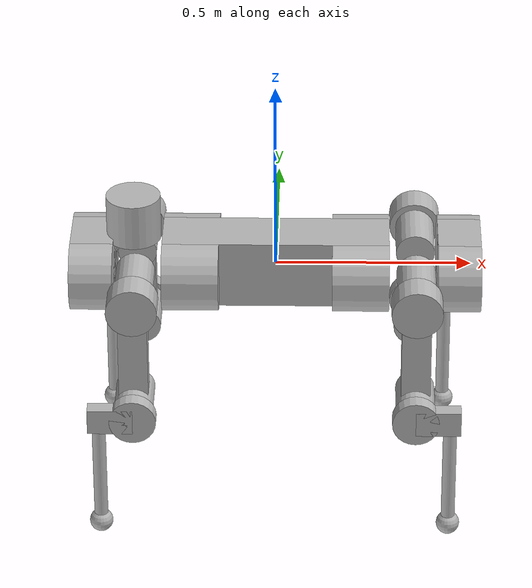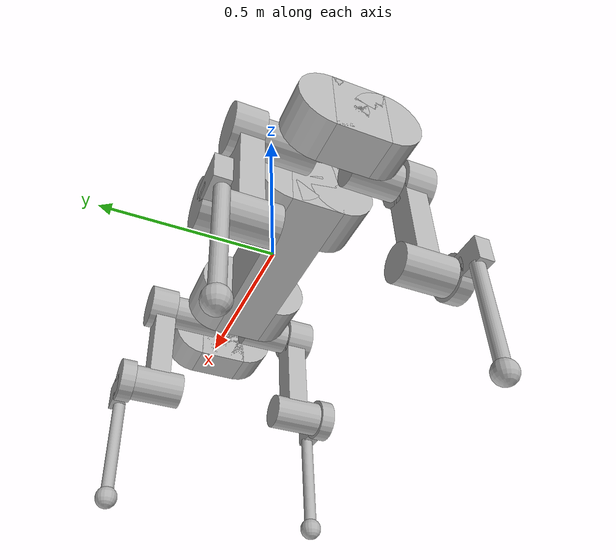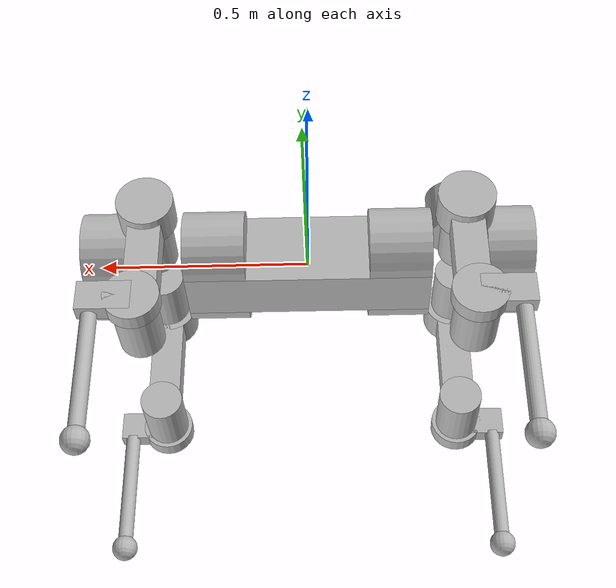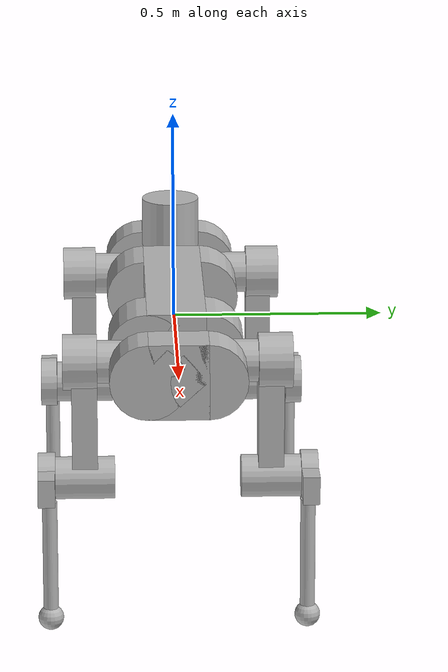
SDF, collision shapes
<sdf version='1.11'>
	<model name='anymal'>
		<!-- 悬挂模型，用于调试 -->
		<link name='base'>
			<inertial>
				<pose>-0.017793943143734711 -0.00017816961328741469 0.0085043390156462131 0 0 0</pose>
				<mass>26.373170000000009</mass>
				<inertia>
					<ixx>0.21671174330797921</ixx>
					<ixy>0.0092238113073508411</ixy>
					<ixz>0.058933188704784728</ixz>
					<iyy>1.785161688617307</iyy>
					<iyz>-0.0001637780172926634</iyz>
					<izz>1.8336994495846779</izz>
				</inertia>
			</inertial>
			<collision name='base_collision'>
				<pose>0 0 0 0 0 0</pose>
				<geometry>
					<box>
						<size>0.57999999999999996 0.14000000000000001 0.17999999999999999</size>
					</box>
				</geometry>
			</collision>
			<collision name='base_collision_1'>
				<pose>0.2175 0.070000000000000007 0 0 1.5707963267948966 0</pose>
				<geometry>
					<cylinder>
						<length>0.14499999999999999</length>
						<radius>0.089999999999999997</radius>
					</cylinder>
				</geometry>
			</collision>
			<collision name='base_collision_2'>
				<pose>-0.2175 0.070000000000000007 0 0 1.5707963267948966 0</pose>
				<geometry>
					<cylinder>
						<length>0.14499999999999999</length>
						<radius>0.089999999999999997</radius>
					</cylinder>
				</geometry>
			</collision>
			<collision name='base_collision_3'>
				<pose>0.2175 -0.070000000000000007 0 0 1.5707963267948966 0</pose>
				<geometry>
					<cylinder>
						<length>0.14499999999999999</length>
						<radius>0.089999999999999997</radius>
					</cylinder>
				</geometry>
			</collision>
			<collision name='base_collision_4'>
				<pose>-0.2175 -0.070000000000000007 0 0 1.5707963267948966 0</pose>
				<geometry>
					<cylinder>
						<length>0.14499999999999999</length>
						<radius>0.089999999999999997</radius>
					</cylinder>
				</geometry>
			</collision>
			<collision name='base_fixed_joint_lump__face_front_collision_5'>
				<pose>0.46949999999999997 0 0 0 0 0</pose>
				<geometry>
					<box>
						<size>0.11 0.14000000000000001 0.17999999999999999</size>
					</box>
				</geometry>
			</collision>
			<collision name='base_fixed_joint_lump__face_front_collision_6'>
				<pose>0.46949999999999997 0.070000000000000007 0 0 1.5707963267948966 0</pose>
				<geometry>
					<cylinder>
						<length>0.11</length>
						<radius>0.089999999999999997</radius>
					</cylinder>
				</geometry>
			</collision>
			<collision name='base_fixed_joint_lump__face_front_collision_7'>
				<pose>0.46949999999999997 -0.070000000000000007 0 0 1.5707963267948966 0</pose>
				<geometry>
					<cylinder>
						<length>0.11</length>
						<radius>0.089999999999999997</radius>
					</cylinder>
				</geometry>
			</collision>
			<collision name='base_fixed_joint_lump__face_rear_collision_8'>
				<pose>-0.46949999999999997 -1.137527089106179e-14 0 0 0 -3.1415926535895871</pose>
				<geometry>
					<box>
						<size>0.11 0.14000000000000001 0.17999999999999999</size>
					</box>
				</geometry>
			</collision>
			<collision name='base_fixed_joint_lump__face_rear_collision_9'>
				<pose>-0.46949999999998548 -0.070000000000011386 0 3.1415926535895866
					1.5707963267948966 0</pose>
				<geometry>
					<cylinder>
						<length>0.11</length>
						<radius>0.089999999999999997</radius>
					</cylinder>
				</geometry>
			</collision>
			<collision name='base_fixed_joint_lump__face_rear_collision_10'>
				<pose>-0.46950000000001452 0.069999999999988627 0 3.1415926535895866
					1.5707963267948966 0</pose>
				<geometry>
					<cylinder>
						<length>0.11</length>
						<radius>0.089999999999999997</radius>
					</cylinder>
				</geometry>
			</collision>
			<collision name='base_fixed_joint_lump__lidar_cage_collision_11'>
				<pose>-0.36399999999999999 0 0.13350000000000001 0 0 0</pose>
				<geometry>
					<cylinder>
						<length>0.12</length>
						<radius>0.070000000000000007</radius>
					</cylinder>
				</geometry>
			</collision>
			<collision name='base_fixed_joint_lump__imu_link_collision_12'>
				<pose>0.24879999999999999 0.0083499999999999998 0.051279999999999999 0 0
					1.57079632679</pose>
				<geometry>
					<box>
						<size>0.024 0.024 0.01</size>
					</box>
				</geometry>
			</collision>
			<visual name='base_visual'>
				<pose>0 0 0 0 0 0</pose>
				<geometry>
					<mesh>
						<scale>1 1 1</scale>
						<uri>meshes/base.dae</uri>
					</mesh>
				</geometry>
			</visual>
			<visual name='base_fixed_joint_lump__LF_HAA_link_visual_1'>
				<pose>0.2999 0.104 0 2.6179938779900001 0 0</pose>
				<geometry>
					<mesh>
						<scale>1 1 1</scale>
						<uri>meshes/drive.dae</uri>
					</mesh>
				</geometry>
			</visual>
			<visual name='base_fixed_joint_lump__LH_HAA_link_visual_2'>
				<pose>-0.2999 0.104 0 -2.6179938779900001 -6.3108872417680944e-30 3.1415926535895871</pose>
				<geometry>
					<mesh>
						<scale>1 1 1</scale>
						<uri>meshes/drive.dae</uri>
					</mesh>
				</geometry>
			</visual>
			<visual name='base_fixed_joint_lump__RF_HAA_link_visual_3'>
				<pose>0.2999 -0.104 0 -2.6179938779900001 0 0</pose>
				<geometry>
					<mesh>
						<scale>1 1 1</scale>
						<uri>meshes/drive.dae</uri>
					</mesh>
				</geometry>
			</visual>
			<visual name='base_fixed_joint_lump__RH_HAA_link_visual_4'>
				<pose>-0.2999 -0.104 0 2.6179938779900001 6.3108872417680944e-30 3.1415926535895871</pose>
				<geometry>
					<mesh>
						<scale>1 1 1</scale>
						<uri>meshes/drive.dae</uri>
					</mesh>
				</geometry>
			</visual>
			<visual name='base_fixed_joint_lump__battery_visual_5'>
				<pose>0 0 0 0 0 0</pose>
				<geometry>
					<mesh>
						<scale>1 1 1</scale>
						<uri>meshes/battery.dae</uri>
					</mesh>
				</geometry>
			</visual>
			<visual name='base_fixed_joint_lump__bottom_shell_visual_6'>
				<pose>0 0 0 0 0 0</pose>
				<geometry>
					<mesh>
						<scale>1 1 1</scale>
						<uri>meshes/bottom_shell.dae</uri>
					</mesh>
				</geometry>
			</visual>
			<visual name='base_fixed_joint_lump__face_front_visual_7'>
				<pose>0.41449999999999998 0 0 0 0 0</pose>
				<geometry>
					<mesh>
						<scale>1 1 1</scale>
						<uri>meshes/face.dae</uri>
					</mesh>
				</geometry>
			</visual>
			<visual name='base_fixed_joint_lump__depth_camera_front_camera_visual_8'>
				<pose>0.46165 0 -0.0292 0 0.52359877559800005 0</pose>
				<geometry>
					<mesh>
						<scale>1 1 1</scale>
						<uri>meshes/depth_camera.dae</uri>
					</mesh>
				</geometry>
			</visual>
			<visual name='base_fixed_joint_lump__wide_angle_camera_front_camera_visual_9'>
				<pose>0.51300000000000001 0 0.014970000000000001 0 0 0</pose>
				<geometry>
					<mesh>
						<scale>1 1 1</scale>
						<uri>meshes/wide_angle_camera.dae</uri>
					</mesh>
				</geometry>
			</visual>
			<visual name='base_fixed_joint_lump__face_rear_visual_10'>
				<pose>-0.41449999999999998 0 0 0 0 -3.1415926535895871</pose>
				<geometry>
					<mesh>
						<scale>1 1 1</scale>
						<uri>meshes/face.dae</uri>
					</mesh>
				</geometry>
			</visual>
			<visual name='base_fixed_joint_lump__depth_camera_rear_camera_visual_11'>
				<pose>-0.46165 -9.7517095002466099e-15 -0.0292 -7.287184895719111e-30
					0.52359877559800005
					-3.1415926535895871</pose>
				<geometry>
					<mesh>
						<scale>1 1 1</scale>
						<uri>meshes/depth_camera.dae</uri>
					</mesh>
				</geometry>
			</visual>
			<visual name='base_fixed_joint_lump__wide_angle_camera_rear_camera_visual_12'>
				<pose>-0.51300000000000001 -2.037207605035612e-14 0.014970000000000001 0 0
					-3.1415926535895871</pose>
				<geometry>
					<mesh>
						<scale>1 1 1</scale>
						<uri>meshes/wide_angle_camera.dae</uri>
					</mesh>
				</geometry>
			</visual>
			<visual name='base_fixed_joint_lump__handle_visual_13'>
				<pose>0 0 0 0 0 0</pose>
				<geometry>
					<mesh>
						<scale>1 1 1</scale>
						<uri>meshes/handle.dae</uri>
					</mesh>
				</geometry>
			</visual>
			<visual name='base_fixed_joint_lump__hatch_visual_14'>
				<pose>0.11600000000000001 0 0.072999999999999995 0 0 0</pose>
				<geometry>
					<mesh>
						<scale>1 1 1</scale>
						<uri>meshes/hatch.dae</uri>
					</mesh>
				</geometry>
			</visual>
			<visual name='base_fixed_joint_lump__remote_visual_15'>
				<pose>0 0 0 0 0 0</pose>
				<geometry>
					<mesh>
						<scale>1 1 1</scale>
						<uri>meshes/remote.dae</uri>
					</mesh>
				</geometry>
			</visual>
			<visual name='base_fixed_joint_lump__depth_camera_left_camera_visual_16'>
				<pose>0 0.07646 0.029049999999999999 -3.2049378106387202e-17 0.52359877559800005
					1.5707963267899998</pose>
				<geometry>
					<mesh>
						<scale>1 1 1</scale>
						<uri>meshes/depth_camera.dae</uri>
					</mesh>
				</geometry>
			</visual>
			<visual name='base_fixed_joint_lump__depth_camera_right_camera_visual_17'>
				<pose>0 -0.07646 0.029049999999999999 3.2049378106387202e-17 0.52359877559800005
					-1.5707963267899998</pose>
				<geometry>
					<mesh>
						<scale>1 1 1</scale>
						<uri>meshes/depth_camera.dae</uri>
					</mesh>
				</geometry>
			</visual>
			<visual name='base_fixed_joint_lump__lidar_cage_visual_18'>
				<pose>-0.36399999999999999 0 0.073499999999999996 0 0 0</pose>
				<geometry>
					<mesh>
						<scale>1 1 1</scale>
						<uri>meshes/lidar_cage.dae</uri>
					</mesh>
				</geometry>
			</visual>
			<visual name='base_fixed_joint_lump__lidar_visual_19'>
				<pose>-0.36399999999999999 0 0.14219999999999999 0 0 -1.57079632679</pose>
				<geometry>
					<mesh>
						<scale>1 1 1</scale>
						<uri>meshes/lidar.dae</uri>
					</mesh>
				</geometry>
			</visual>
			<visual name='base_fixed_joint_lump__top_shell_visual_20'>
				<pose>0 0 0 0 0 0</pose>
				<geometry>
					<mesh>
						<scale>1 1 1</scale>
						<uri>meshes/top_shell.dae</uri>
					</mesh>
				</geometry>
			</visual>
			<visual name='base_fixed_joint_lump__imu_link_visual_21'>
				<pose>0.24879999999999999 0.0083499999999999998 0.051279999999999999 0 0
					1.57079632679</pose>
				<geometry>
					<box>
						<size>0.024 0.024 0.01</size>
					</box>
				</geometry>
			</visual>
			<sensor name="imu_sensor" type="imu">
				<always_on>1</always_on>
				<update_rate>1</update_rate>
				<visualize>true</visualize>
				<topic>/anymal/imu</topic>
			</sensor>
		</link>
		<joint name='LF_HAA' type='revolute'>
			<pose relative_to='base'>0.2999 0.104 0 2.6179938779900001 0 0</pose>
			<parent>base</parent>
			<child>LF_HIP</child>
			<axis>
				<xyz>1 0 0</xyz>
				<limit>
					<lower>-0.71999999999999997</lower>
					<upper>0.48999999999999999</upper>
					<effort>80</effort>
					<velocity>7.5</velocity>
				</limit>
				<dynamics>
					<damping>0.01</damping>
					<friction>0.01</friction>
					<spring_reference>0</spring_reference>
					<spring_stiffness>0</spring_stiffness>
				</dynamics>
			</axis>
		</joint>
		<link name='LF_HIP'>
			<pose relative_to='LF_HAA'>0 0 0 0 0 0</pose>
			<inertial>
				<pose>0.056660625673991612 -0.015293968803304031 -0.0082978431652548611 0 0 0</pose>
				<mass>2.7810000000000001</mass>
				<inertia>
					<ixx>0.003295526429711179</ixx>
					<ixy>-1.0388233058723431e-05</ixy>
					<ixz>0.0001070622327342813</ixz>
					<iyy>0.0050443492876884287</iyy>
					<iyz>-0.00031949181072328699</iyz>
					<izz>0.0057269038510383181</izz>
				</inertia>
			</inertial>
			<collision name='LF_HIP_fixed_joint_lump__LF_HFE_link_collision'>
				<pose>0.059899999999657227 -0.011959810826252771 -0.0069050000000178656
					-3.141592653584897
					-1.0471975511902076 -1.570796326794897</pose>
				<geometry>
					<cylinder>
						<length>0.14000000000000001</length>
						<radius>0.050000000000000003</radius>
					</cylinder>
				</geometry>
			</collision>
			<visual name='LF_HIP_fixed_joint_lump__LF_hip_fixed_visual'>
				<pose>0 0 0 -2.6179938779900001 0 0</pose>
				<geometry>
					<mesh>
						<scale>1 1 1</scale>
						<uri>meshes/hip_l.dae</uri>
					</mesh>
				</geometry>
			</visual>
			<visual name='LF_HIP_fixed_joint_lump__LF_HFE_link_visual_1'>
				<pose>0.059900000000000002 -0.072581589091111176 -0.041905000000108453
					-3.141592653586966
					0.52359877559979318 -1.570796326789242</pose>
				<geometry>
					<mesh>
						<scale>1 1 1</scale>
						<uri>meshes/drive.dae</uri>
					</mesh>
				</geometry>
			</visual>
		</link>
		<joint name='LF_HFE' type='revolute'>
			<pose relative_to='LF_HIP'>0.059900000000000002 -0.072581589091111176
				-0.041905000000108453
				-3.141592653586966 0.52359877559979318 -1.570796326789242</pose>
			<parent>LF_HIP</parent>
			<child>LF_THIGH</child>
			<axis>
				<xyz>1 0 0</xyz>
				<limit>
					<lower>-9.4247779607699993</lower>
					<upper>9.4247779607699993</upper>
					<effort>80</effort>
					<velocity>7.5</velocity>
				</limit>
				<dynamics>
					<damping>0.01</damping>
					<friction>0.01</friction>
					<spring_reference>0</spring_reference>
					<spring_stiffness>0</spring_stiffness>
				</dynamics>
			</axis>
		</joint>
		<link name='LF_THIGH'>
			<pose relative_to='LF_HFE'>0 0 0 0 0 0</pose>
			<inertial>
				<pose>0.03081471833279063 4.6499511915559621e-05 -0.24569573428850541 0 0 0</pose>
				<mass>3.0710000000000002</mass>
				<inertia>
					<ixx>0.029563793513988971</ixx>
					<ixy>4.4291901775859802e-05</ixy>
					<ixz>0.0041424259528102039</ixz>
					<iyy>0.029904049332850569</iyy>
					<iyz>9.4479961187896678e-05</iyz>
					<izz>0.004861084530601148</izz>
				</inertia>
			</inertial>
			<collision name='LF_THIGH_fixed_joint_lump__LF_thigh_fixed_collision'>
				<pose>0.040000000000000001 1.9587109711949319e-13 0 1.57079632679
					5.5511151231257827e-17
					-1.57079632679</pose>
				<geometry>
					<cylinder>
						<length>0.080000000000000002</length>
						<radius>0.065000000000000002</radius>
					</cylinder>
				</geometry>
			</collision>
			<collision name='LF_THIGH_fixed_joint_lump__LF_thigh_fixed_collision_1'>
				<pose>0.029999999999999999 1.46899853392668e-13 -0.14131350000000001 0 0
					-1.57079632679</pose>
				<geometry>
					<box>
						<size>0.074999999999999997 0.059999999999999998 0.28262700000000002</size>
					</box>
				</geometry>
			</collision>
			<collision name='LF_THIGH_fixed_joint_lump__LF_KFE_link_collision_2'>
				<pose>0.03029999999999999 4.9113837996550558e-13 -0.28499999999999998 0
					1.5707963267948966 0</pose>
				<geometry>
					<cylinder>
						<length>0.14000000000000001</length>
						<radius>0.050000000000000003</radius>
					</cylinder>
				</geometry>
			</collision>
			<visual name='LF_THIGH_fixed_joint_lump__LF_thigh_fixed_visual'>
				<pose>0 0 0 0 0 -1.57079632679</pose>
				<geometry>
					<mesh>
						<scale>1 1 1</scale>
						<uri>meshes/thigh.dae</uri>
					</mesh>
				</geometry>
			</visual>
			<visual name='LF_THIGH_fixed_joint_lump__LF_KFE_link_visual_1'>
				<pose>0.1003 4.9113491051855362e-13 -0.28499999999999998 0 0 0</pose>
				<geometry>
					<mesh>
						<scale>1 1 1</scale>
						<uri>meshes/drive.dae</uri>
					</mesh>
				</geometry>
			</visual>
		</link>
		<joint name='LF_KFE' type='revolute'>
			<pose relative_to='LF_THIGH'>0.1003 4.9113491051855362e-13 -0.28499999999999998 0 0 0</pose>
			<parent>LF_THIGH</parent>
			<child>LF_SHANK</child>
			<axis>
				<xyz>1 0 0</xyz>
				<limit>
					<lower>-9.4247779607699993</lower>
					<upper>9.4247779607699993</upper>
					<effort>80</effort>
					<velocity>7.5</velocity>
				</limit>
				<dynamics>
					<damping>0.01</damping>
					<friction>0.01</friction>
					<spring_reference>0</spring_reference>
					<spring_stiffness>0</spring_stiffness>
				</dynamics>
			</axis>
		</joint>
		<link name='LF_SHANK'>
			<pose relative_to='LF_KFE'>0 0 0 0 0 0</pose>
			<inertial>
				<pose>0.0054619992525347279 -0.061252769450365827 -0.080659781108731843 0 0 0</pose>
				<mass>0.58842000000000005</mass>
				<inertia>
					<ixx>0.010161141436439239</ixx>
					<ixy>-5.3571329219367323e-05</ixy>
					<ixz>-2.2660426829587631e-05</ixz>
					<iyy>0.0088103798213393578</iyy>
					<iyz>-0.001819353694812817</iyz>
					<izz>0.0015497840809709841</izz>
				</inertia>
			</inertial>
			<collision name='LF_SHANK_fixed_joint_lump__LF_shank_fixed_collision'>
				<pose>0.02 9.7935548559746621e-14 0 1.57079632679 5.5511151231257827e-17
					-1.57079632679</pose>
				<geometry>
					<cylinder>
						<length>0.040000000000000001</length>
						<radius>0.059999999999999998</radius>
					</cylinder>
				</geometry>
			</collision>
			<collision name='LF_SHANK_fixed_joint_lump__LF_shank_fixed_collision_1'>
				<pose>0.02000000000028155 -0.057498999999902073 0 1.57079632679
					5.5511151231257827e-17
					-1.57079632679</pose>
				<geometry>
					<box>
						<size>0.114998 0.067500000000000004 0.040000000000000001</size>
					</box>
				</geometry>
			</collision>
			<collision name='LF_SHANK_fixed_joint_lump__LF_FOOT_collision_2'>
				<pose>0.01305000000043066 -0.087949999999936093 -0.168985 0 0 -1.57079632679</pose>
				<geometry>
					<cylinder>
						<length>0.28250399999999998</length>
						<radius>0.017500000000000002</radius>
					</cylinder>
				</geometry>
			</collision>
			<collision name='LF_SHANK_fixed_joint_lump__LF_FOOT_collision_3'>
				<pose>0.01305000000043066 -0.087949999999936093 -0.31546999999999997 0 0
					-1.57079632679</pose>
				<geometry>
					<sphere>
						<radius>0.029999999999999999</radius>
					</sphere>
				</geometry>
			</collision>
			<visual name='LF_SHANK_fixed_joint_lump__LF_shank_fixed_visual'>
				<pose>0 0 0 0 0 -1.57079632679</pose>
				<geometry>
					<mesh>
						<scale>1 1 1</scale>
						<uri>meshes/shank_l.dae</uri>
					</mesh>
				</geometry>
			</visual>
			<visual name='LF_SHANK_fixed_joint_lump__LF_FOOT_visual_1'>
				<pose>0.01305000000043066 -0.087949999999936093 -0.33796999999999999 0 0
					-2.3561944901869998</pose>
				<geometry>
					<mesh>
						<scale>1 1 1</scale>
						<uri>meshes/foot.dae</uri>
					</mesh>
				</geometry>
			</visual>
			<sensor name="lf_foot_contact" type="contact">
				<always_on>1</always_on>
				<update_rate>200</update_rate>
				<topic>/anymal/LF/contact</topic>
				<contact>
					<collision>LF_SHANK_fixed_joint_lump__LF_FOOT_collision_3</collision>
				</contact>
			</sensor>
		</link>
		<joint name='LH_HAA' type='revolute'>
			<pose relative_to='base'>-0.2999 0.104 0 -2.6179938779900001 -6.3108872417680944e-30
				3.1415926535895871</pose>
			<parent>base</parent>
			<child>LH_HIP</child>
			<axis>
				<xyz>-1 0 0</xyz>
				<limit>
					<lower>-0.71999999999999997</lower>
					<upper>0.48999999999999999</upper>
					<effort>80</effort>
					<velocity>7.5</velocity>
				</limit>
				<dynamics>
					<damping>0.01</damping>
					<friction>0.01</friction>
					<spring_reference>0</spring_reference>
					<spring_stiffness>0</spring_stiffness>
				</dynamics>
			</axis>
		</joint>
		<link name='LH_HIP'>
			<pose relative_to='LH_HAA'>0 0 0 0 0 0</pose>
			<inertial>
				<pose>0.056763322546076272 0.015293968803292301 -0.0082978431652548611 0 0 0</pose>
				<mass>2.7810000000000001</mass>
				<inertia>
					<ixx>0.0032955264297111742</ixx>
					<ixy>-1.1005261347922599e-05</ixy>
					<ixz>-0.00010912110284194391</ixz>
					<iyy>0.0050461702880848017</iyy>
					<iyz>0.00031949181072330873</iyz>
					<izz>0.0057287248514346816</izz>
				</inertia>
			</inertial>
			<collision name='LH_HIP_fixed_joint_lump__LH_HFE_link_collision'>
				<pose>0.059900000000345253 0.011959810826240379 -0.0069050000000178656
					-3.1415926535848975
					-1.0471975511902067 1.5707963267946903</pose>
				<geometry>
					<cylinder>
						<length>0.14000000000000001</length>
						<radius>0.050000000000000003</radius>
					</cylinder>
				</geometry>
			</collision>
			<visual name='LH_HIP_fixed_joint_lump__LH_hip_fixed_visual'>
				<pose>0 0 0 2.6179938779900001 1.0341155355537489e-13 -2.7709042263293297e-14</pose>
				<geometry>
					<mesh>
						<scale>1 1 1</scale>
						<uri>meshes/hip_r.dae</uri>
					</mesh>
				</geometry>
			</visual>
			<visual name='LH_HIP_fixed_joint_lump__LH_HFE_link_visual_1'>
				<pose>0.059900000000014997 0.072581589091098797 -0.041905000000108453
					-3.141592653586966
					0.52359877559979318 1.5707963268003442</pose>
				<geometry>
					<mesh>
						<scale>1 1 1</scale>
						<uri>meshes/drive.dae</uri>
					</mesh>
				</geometry>
			</visual>
		</link>
		<joint name='LH_HFE' type='revolute'>
			<pose relative_to='LH_HIP'>0.059900000000014997 0.072581589091098797
				-0.041905000000108453
				-3.141592653586966 0.52359877559979318 1.5707963268003442</pose>
			<parent>LH_HIP</parent>
			<child>LH_THIGH</child>
			<axis>
				<xyz>1 0 0</xyz>
				<limit>
					<lower>-9.4247779607699993</lower>
					<upper>9.4247779607699993</upper>
					<effort>80</effort>
					<velocity>7.5</velocity>
				</limit>
				<dynamics>
					<damping>0.01</damping>
					<friction>0.01</friction>
					<spring_reference>0</spring_reference>
					<spring_stiffness>0</spring_stiffness>
				</dynamics>
			</axis>
		</joint>
		<link name='LH_THIGH'>
			<pose relative_to='LH_HFE'>0 0 0 0 0 0</pose>
			<inertial>
				<pose>0.03081471833279063 4.6499511915559621e-05 -0.24569573428850541 0 0 0</pose>
				<mass>3.0710000000000002</mass>
				<inertia>
					<ixx>0.029563793513988971</ixx>
					<ixy>4.43959017758598e-05</ixy>
					<ixz>0.0041424259528101033</ixz>
					<iyy>0.029904049332850569</iyy>
					<iyz>0.0001147939611878967</iyz>
					<izz>0.004861084530601148</izz>
				</inertia>
			</inertial>
			<collision name='LH_THIGH_fixed_joint_lump__LH_thigh_fixed_collision'>
				<pose>0.040000000000000001 1.9587109711949319e-13 0 1.57079632679
					5.5511151231257827e-17
					-1.57079632679</pose>
				<geometry>
					<cylinder>
						<length>0.080000000000000002</length>
						<radius>0.065000000000000002</radius>
					</cylinder>
				</geometry>
			</collision>
			<collision name='LH_THIGH_fixed_joint_lump__LH_thigh_fixed_collision_1'>
				<pose>0.029999999999999999 1.46899853392668e-13 -0.14131350000000001 0 0
					-1.57079632679</pose>
				<geometry>
					<box>
						<size>0.074999999999999997 0.059999999999999998 0.28262700000000002</size>
					</box>
				</geometry>
			</collision>
			<collision name='LH_THIGH_fixed_joint_lump__LH_KFE_link_collision_2'>
				<pose>0.03029999999999999 4.9113837996550558e-13 -0.28499999999999998 0
					1.5707963267948966 0</pose>
				<geometry>
					<cylinder>
						<length>0.14000000000000001</length>
						<radius>0.050000000000000003</radius>
					</cylinder>
				</geometry>
			</collision>
			<visual name='LH_THIGH_fixed_joint_lump__LH_thigh_fixed_visual'>
				<pose>0 0 0 0 0 -1.57079632679</pose>
				<geometry>
					<mesh>
						<scale>1 1 1</scale>
						<uri>meshes/thigh.dae</uri>
					</mesh>
				</geometry>
			</visual>
			<visual name='LH_THIGH_fixed_joint_lump__LH_KFE_link_visual_1'>
				<pose>0.1003 4.9113491051855362e-13 -0.28499999999999998 0 0 0</pose>
				<geometry>
					<mesh>
						<scale>1 1 1</scale>
						<uri>meshes/drive.dae</uri>
					</mesh>
				</geometry>
			</visual>
		</link>
		<joint name='LH_KFE' type='revolute'>
			<pose relative_to='LH_THIGH'>0.1003 4.9113491051855362e-13 -0.28499999999999998 0 0 0</pose>
			<parent>LH_THIGH</parent>
			<child>LH_SHANK</child>
			<axis>
				<xyz>1 0 0</xyz>
				<limit>
					<lower>-9.4247779607699993</lower>
					<upper>9.4247779607699993</upper>
					<effort>80</effort>
					<velocity>7.5</velocity>
				</limit>
				<dynamics>
					<damping>0.01</damping>
					<friction>0.01</friction>
					<spring_reference>0</spring_reference>
					<spring_stiffness>0</spring_stiffness>
				</dynamics>
			</axis>
		</joint>
		<link name='LH_SHANK'>
			<pose relative_to='LH_KFE'>0 0 0 0 0 0</pose>
			<inertial>
				<pose>0.0054619992519348683 0.061252769450419318 -0.080659781108731843 0 0 0</pose>
				<mass>0.58842000000000005</mass>
				<inertia>
					<ixx>0.010161141436438179</ixx>
					<ixy>5.3571329232595592e-05</ixy>
					<ixz>-2.2660426847404861e-05</ixz>
					<iyy>0.008810379821340409</iyy>
					<iyz>0.001819353694812596</iyz>
					<izz>0.0015497840809709841</izz>
				</inertia>
			</inertial>
			<collision name='LH_SHANK_fixed_joint_lump__LH_shank_fixed_collision'>
				<pose>0.02 9.7935548559746621e-14 0 1.57079632679 5.5511151231257827e-17
					-1.57079632679</pose>
				<geometry>
					<cylinder>
						<length>0.040000000000000001</length>
						<radius>0.059999999999999998</radius>
					</cylinder>
				</geometry>
			</collision>
			<collision name='LH_SHANK_fixed_joint_lump__LH_shank_fixed_collision_1'>
				<pose>0.019999999999718441 0.05749900000009793 0 1.57079632679
					5.5511151231257827e-17
					-1.57079632679</pose>
				<geometry>
					<box>
						<size>0.114998 0.067500000000000004 0.040000000000000001</size>
					</box>
				</geometry>
			</collision>
			<collision name='LH_SHANK_fixed_joint_lump__LH_FOOT_collision_2'>
				<pose>0.013049999999569351 0.087950000000063908 -0.168985 0 0 -1.57079632679</pose>
				<geometry>
					<cylinder>
						<length>0.28250399999999998</length>
						<radius>0.017500000000000002</radius>
					</cylinder>
				</geometry>
			</collision>
			<collision name='LH_SHANK_fixed_joint_lump__LH_FOOT_collision_3'>
				<pose>0.013049999999569351 0.087950000000063908 -0.31546999999999997 0 0
					-1.57079632679</pose>
				<geometry>
					<sphere>
						<radius>0.029999999999999999</radius>
					</sphere>
				</geometry>
			</collision>
			<visual name='LH_SHANK_fixed_joint_lump__LH_shank_fixed_visual'>
				<pose>0 0 0 0 0 1.5707963267995859</pose>
				<geometry>
					<mesh>
						<scale>1 1 1</scale>
						<uri>meshes/shank_r.dae</uri>
					</mesh>
				</geometry>
			</visual>
			<visual name='LH_SHANK_fixed_joint_lump__LH_FOOT_visual_1'>
				<pose>0.013049999999569351 0.087950000000063908 -0.33796999999999999 0 0
					2.356194490199587</pose>
				<geometry>
					<mesh>
						<scale>1 1 1</scale>
						<uri>meshes/foot.dae</uri>
					</mesh>
				</geometry>
			</visual>
			<sensor name="lh_foot_contact" type="contact">
				<always_on>1</always_on>
				<update_rate>200</update_rate>
				<topic>/anymal/LH/contact</topic>
				<contact>
					<collision>LH_SHANK_fixed_joint_lump__LH_FOOT_collision_3</collision>
				</contact>
			</sensor>
		</link>
		<joint name='RF_HAA' type='revolute'>
			<pose relative_to='base'>0.2999 -0.104 0 -2.6179938779900001 0 0</pose>
			<parent>base</parent>
			<child>RF_HIP</child>
			<axis>
				<xyz>1 0 0</xyz>
				<limit>
					<lower>-0.48999999999999999</lower>
					<upper>0.71999999999999997</upper>
					<effort>80</effort>
					<velocity>7.5</velocity>
				</limit>
				<dynamics>
					<damping>0.01</damping>
					<friction>0.01</friction>
					<spring_reference>0</spring_reference>
					<spring_stiffness>0</spring_stiffness>
				</dynamics>
			</axis>
		</joint>
		<link name='RF_HIP'>
			<pose relative_to='RF_HAA'>0 0 0 0 0 0</pose>
			<inertial>
				<pose>0.056763322545620533 0.01529396880330359 -0.0082978431652546061 0 0 0</pose>
				<mass>2.7810000000000001</mass>
				<inertia>
					<ixx>0.003295526429712052</ixx>
					<ixy>-1.1005261351951489e-05</ixy>
					<ixz>-0.0001091211028422321</ixz>
					<iyy>0.0050461702880768983</iyy>
					<iyz>0.00031949181072414942</iyz>
					<izz>0.0057287248514255439</izz>
				</inertia>
			</inertial>
			<collision name='RF_HIP_fixed_joint_lump__RF_HFE_link_collision'>
				<pose>0.059899999999657227 0.011959810826252771 -0.0069050000000178656
					3.141592653584897
					-1.0471975511902076 1.570796326794897</pose>
				<geometry>
					<cylinder>
						<length>0.14000000000000001</length>
						<radius>0.050000000000000003</radius>
					</cylinder>
				</geometry>
			</collision>
			<visual name='RF_HIP_fixed_joint_lump__RF_hip_fixed_visual'>
				<pose>0 0 0 2.6179938779900001 0 0</pose>
				<geometry>
					<mesh>
						<scale>1 1 1</scale>
						<uri>meshes/hip_r.dae</uri>
					</mesh>
				</geometry>
			</visual>
			<visual name='RF_HIP_fixed_joint_lump__RF_HFE_link_visual_1'>
				<pose>0.059900000000000002 0.072581589091111176 -0.041905000000108453
					3.141592653586966
					0.52359877559979318 1.570796326789242</pose>
				<geometry>
					<mesh>
						<scale>1 1 1</scale>
						<uri>meshes/drive.dae</uri>
					</mesh>
				</geometry>
			</visual>
		</link>
		<joint name='RF_HFE' type='revolute'>
			<pose relative_to='RF_HIP'>0.059900000000000002 0.072581589091111176
				-0.041905000000108453
				3.141592653586966 0.52359877559979318 1.570796326789242</pose>
			<parent>RF_HIP</parent>
			<child>RF_THIGH</child>
			<axis>
				<xyz>-1 0 0</xyz>
				<limit>
					<lower>-9.4247779607699993</lower>
					<upper>9.4247779607699993</upper>
					<effort>80</effort>
					<velocity>7.5</velocity>
				</limit>
				<dynamics>
					<damping>0.01</damping>
					<friction>0.01</friction>
					<spring_reference>0</spring_reference>
					<spring_stiffness>0</spring_stiffness>
				</dynamics>
			</axis>
		</joint>
		<link name='RF_THIGH'>
			<pose relative_to='RF_HFE'>0 0 0 0 0 0</pose>
			<inertial>
				<pose>0.030814718332790619 4.6499511203945423e-05 -0.24569573428850541 0 0 0</pose>
				<mass>3.0710000000000002</mass>
				<inertia>
					<ixx>0.029563793513988881</ixx>
					<ixy>4.4395901779985203e-05</ixy>
					<ixz>0.0041424259528102074</ixz>
					<iyy>0.029904049332850541</iyy>
					<iyz>0.0001147939610993062</iyz>
					<izz>0.0048610845306010673</izz>
				</inertia>
			</inertial>
			<collision name='RF_THIGH_fixed_joint_lump__RF_thigh_fixed_collision'>
				<pose>0.040000000000000001 -1.9587109711949319e-13 0 1.57079632679
					-5.5511151231257827e-17
					1.57079632679</pose>
				<geometry>
					<cylinder>
						<length>0.080000000000000002</length>
						<radius>0.065000000000000002</radius>
					</cylinder>
				</geometry>
			</collision>
			<collision name='RF_THIGH_fixed_joint_lump__RF_thigh_fixed_collision_1'>
				<pose>0.029999999999999999 -1.46899853392668e-13 -0.14131350000000001 0 0
					1.57079632679</pose>
				<geometry>
					<box>
						<size>0.074999999999999997 0.059999999999999998 0.28262700000000002</size>
					</box>
				</geometry>
			</collision>
			<collision name='RF_THIGH_fixed_joint_lump__RF_KFE_link_collision_2'>
				<pose>0.03029999999999999 -4.9113837996550558e-13 -0.28499999999999998 0
					1.5707963267948966
					0</pose>
				<geometry>
					<cylinder>
						<length>0.14000000000000001</length>
						<radius>0.050000000000000003</radius>
					</cylinder>
				</geometry>
			</collision>
			<visual name='RF_THIGH_fixed_joint_lump__RF_thigh_fixed_visual'>
				<pose>0 0 0 0 0 -1.5707963268</pose>
				<geometry>
					<mesh>
						<scale>1 1 1</scale>
						<uri>meshes/thigh.dae</uri>
					</mesh>
				</geometry>
			</visual>
			<visual name='RF_THIGH_fixed_joint_lump__RF_KFE_link_visual_1'>
				<pose>0.1003 -4.9113491051855362e-13 -0.28499999999999998 0 0 0</pose>
				<geometry>
					<mesh>
						<scale>1 1 1</scale>
						<uri>meshes/drive.dae</uri>
					</mesh>
				</geometry>
			</visual>
		</link>
		<joint name='RF_KFE' type='revolute'>
			<pose relative_to='RF_THIGH'>0.1003 -4.9113491051855362e-13 -0.28499999999999998 0 0 0</pose>
			<parent>RF_THIGH</parent>
			<child>RF_SHANK</child>
			<axis>
				<xyz>-1 0 0</xyz>
				<limit>
					<lower>-9.4247779607699993</lower>
					<upper>9.4247779607699993</upper>
					<effort>80</effort>
					<velocity>7.5</velocity>
				</limit>
				<dynamics>
					<damping>0.01</damping>
					<friction>0.01</friction>
					<spring_reference>0</spring_reference>
					<spring_stiffness>0</spring_stiffness>
				</dynamics>
			</axis>
		</joint>
		<link name='RF_SHANK'>
			<pose relative_to='RF_KFE'>0 0 0 0 0 0</pose>
			<inertial>
				<pose>0.0054619992525347279 0.061252769450365827 -0.080659781108731843 0 0 0</pose>
				<mass>0.58842000000000005</mass>
				<inertia>
					<ixx>0.010161141436439239</ixx>
					<ixy>5.3571329219367323e-05</ixy>
					<ixz>-2.2660426829587631e-05</ixz>
					<iyy>0.0088103798213393578</iyy>
					<iyz>0.001819353694812817</iyz>
					<izz>0.0015497840809709841</izz>
				</inertia>
			</inertial>
			<collision name='RF_SHANK_fixed_joint_lump__RF_shank_fixed_collision'>
				<pose>0.02 -9.7935548559746621e-14 0 1.57079632679 -5.5511151231257827e-17
					1.57079632679</pose>
				<geometry>
					<cylinder>
						<length>0.040000000000000001</length>
						<radius>0.059999999999999998</radius>
					</cylinder>
				</geometry>
			</collision>
			<collision name='RF_SHANK_fixed_joint_lump__RF_shank_fixed_collision_1'>
				<pose>0.02000000000028155 0.057498999999902073 0 1.57079632679
					-5.5511151231257827e-17
					1.57079632679</pose>
				<geometry>
					<box>
						<size>0.114998 0.067500000000000004 0.040000000000000001</size>
					</box>
				</geometry>
			</collision>
			<collision name='RF_SHANK_fixed_joint_lump__RF_FOOT_collision_2'>
				<pose>0.01305000000043066 0.087949999999936093 -0.168985 0 0 1.57079632679</pose>
				<geometry>
					<cylinder>
						<length>0.28250399999999998</length>
						<radius>0.017500000000000002</radius>
					</cylinder>
				</geometry>
			</collision>
			<collision name='RF_SHANK_fixed_joint_lump__RF_FOOT_collision_3'>
				<pose>0.01305000000043066 0.087949999999936093 -0.31546999999999997 0 0
					1.57079632679</pose>
				<geometry>
					<sphere>
						<radius>0.029999999999999999</radius>
					</sphere>
				</geometry>
			</collision>
			<visual name='RF_SHANK_fixed_joint_lump__RF_shank_fixed_visual'>
				<pose>0 0 0 0 0 1.57079632679</pose>
				<geometry>
					<mesh>
						<scale>1 1 1</scale>
						<uri>meshes/shank_r.dae</uri>
					</mesh>
				</geometry>
			</visual>
			<visual name='RF_SHANK_fixed_joint_lump__RF_FOOT_visual_1'>
				<pose>0.01305000000043066 0.087949999999936093 -0.33796999999999999 0 0
					2.3561944901869998</pose>
				<geometry>
					<mesh>
						<scale>1 1 1</scale>
						<uri>meshes/foot.dae</uri>
					</mesh>
				</geometry>
			</visual>
			<sensor name="rf_foot_contact" type="contact">
				<always_on>1</always_on>
				<update_rate>200</update_rate>
				<topic>/anymal/RF/contact</topic>
				<contact>
					<collision>RF_SHANK_fixed_joint_lump__RF_FOOT_collision_3</collision>
				</contact>
			</sensor>
		</link>
		<joint name='RH_HAA' type='revolute'>
			<pose relative_to='base'>-0.2999 -0.104 0 2.6179938779900001 6.3108872417680944e-30
				3.1415926535895871</pose>
			<parent>base</parent>
			<child>RH_HIP</child>
			<axis>
				<xyz>-1 0 0</xyz>
				<limit>
					<lower>-0.48999999999999999</lower>
					<upper>0.71999999999999997</upper>
					<effort>80</effort>
					<velocity>7.5</velocity>
				</limit>
				<dynamics>
					<damping>0.01</damping>
					<friction>0.01</friction>
					<spring_reference>0</spring_reference>
					<spring_stiffness>0</spring_stiffness>
				</dynamics>
			</axis>
		</joint>
		<link name='RH_HIP'>
			<pose relative_to='RH_HAA'>0 0 0 0 0 0</pose>
			<inertial>
				<pose>0.056660625674441023 -0.015293968803315299 -0.0082978431652546061 0 0 0</pose>
				<mass>2.7810000000000001</mass>
				<inertia>
					<ixx>0.0032955264297120481</ixx>
					<ixy>-1.038823306203805e-05</ixy>
					<ixz>0.0001070622327344326</ixz>
					<iyy>0.0050443492876965819</iyy>
					<iyz>-0.00031949181072417148</iyz>
					<izz>0.0057269038510452223</izz>
				</inertia>
			</inertial>
			<collision name='RH_HIP_fixed_joint_lump__RH_HFE_link_collision'>
				<pose>0.059900000000340292 -0.01195981082626516 -0.0069050000000178656
					3.141592653584897
					-1.0471975511902074 -1.5707963267951028</pose>
				<geometry>
					<cylinder>
						<length>0.14000000000000001</length>
						<radius>0.050000000000000003</radius>
					</cylinder>
				</geometry>
			</collision>
			<visual name='RH_HIP_fixed_joint_lump__RH_hip_fixed_visual'>
				<pose>0 0 0 -2.6179938779900001 -1.0341155355537489e-13 -2.7709042263293297e-14</pose>
				<geometry>
					<mesh>
						<scale>1 1 1</scale>
						<uri>meshes/hip_l.dae</uri>
					</mesh>
				</geometry>
			</visual>
			<visual name='RH_HIP_fixed_joint_lump__RH_HFE_link_visual_1'>
				<pose>0.059899999999984979 -0.072581589091123569 -0.041905000000108453
					3.141592653586966
					0.52359877559979318 -1.5707963268007583</pose>
				<geometry>
					<mesh>
						<scale>1 1 1</scale>
						<uri>meshes/drive.dae</uri>
					</mesh>
				</geometry>
			</visual>
		</link>
		<joint name='RH_HFE' type='revolute'>
			<pose relative_to='RH_HIP'>0.059899999999984979 -0.072581589091123569
				-0.041905000000108453
				3.141592653586966 0.52359877559979318 -1.5707963268007583</pose>
			<parent>RH_HIP</parent>
			<child>RH_THIGH</child>
			<axis>
				<xyz>-1 0 0</xyz>
				<limit>
					<lower>-9.4247779607699993</lower>
					<upper>9.4247779607699993</upper>
					<effort>80</effort>
					<velocity>7.5</velocity>
				</limit>
				<dynamics>
					<damping>0.01</damping>
					<friction>0.01</friction>
					<spring_reference>0</spring_reference>
					<spring_stiffness>0</spring_stiffness>
				</dynamics>
			</axis>
		</joint>
		<link name='RH_THIGH'>
			<pose relative_to='RH_HFE'>0 0 0 0 0 0</pose>
			<inertial>
				<pose>0.030814718332790619 4.6499511203945423e-05 -0.24569573428850541 0 0 0</pose>
				<mass>3.0710000000000002</mass>
				<inertia>
					<ixx>0.029563793513988881</ixx>
					<ixy>4.4291901779985212e-05</ixy>
					<ixz>0.0041424259528101068</ixz>
					<iyy>0.029904049332850541</iyy>
					<iyz>9.4479961099306194e-05</iyz>
					<izz>0.0048610845306010673</izz>
				</inertia>
			</inertial>
			<collision name='RH_THIGH_fixed_joint_lump__RH_thigh_fixed_collision'>
				<pose>0.040000000000000001 -1.9587109711949319e-13 0 1.57079632679
					-5.5511151231257827e-17
					1.57079632679</pose>
				<geometry>
					<cylinder>
						<length>0.080000000000000002</length>
						<radius>0.065000000000000002</radius>
					</cylinder>
				</geometry>
			</collision>
			<collision name='RH_THIGH_fixed_joint_lump__RH_thigh_fixed_collision_1'>
				<pose>0.029999999999999999 -1.46899853392668e-13 -0.14131350000000001 0 0
					1.57079632679</pose>
				<geometry>
					<box>
						<size>0.074999999999999997 0.059999999999999998 0.28262700000000002</size>
					</box>
				</geometry>
			</collision>
			<collision name='RH_THIGH_fixed_joint_lump__RH_KFE_link_collision_2'>
				<pose>0.03029999999999999 -4.9113837996550558e-13 -0.28499999999999998 0
					1.5707963267948966
					0</pose>
				<geometry>
					<cylinder>
						<length>0.14000000000000001</length>
						<radius>0.050000000000000003</radius>
					</cylinder>
				</geometry>
			</collision>
			<visual name='RH_THIGH_fixed_joint_lump__RH_thigh_fixed_visual'>
				<pose>0 0 0 0 0 -1.5707963268</pose>
				<geometry>
					<mesh>
						<scale>1 1 1</scale>
						<uri>meshes/thigh.dae</uri>
					</mesh>
				</geometry>
			</visual>
			<visual name='RH_THIGH_fixed_joint_lump__RH_KFE_link_visual_1'>
				<pose>0.1003 -4.9113491051855362e-13 -0.28499999999999998 0 0 0</pose>
				<geometry>
					<mesh>
						<scale>1 1 1</scale>
						<uri>meshes/drive.dae</uri>
					</mesh>
				</geometry>
			</visual>
		</link>
		<joint name='RH_KFE' type='revolute'>
			<pose relative_to='RH_THIGH'>0.1003 -4.9113491051855362e-13 -0.28499999999999998 0 0 0</pose>
			<parent>RH_THIGH</parent>
			<child>RH_SHANK</child>
			<axis>
				<xyz>-1 0 0</xyz>
				<limit>
					<lower>-9.4247779607699993</lower>
					<upper>9.4247779607699993</upper>
					<effort>80</effort>
					<velocity>7.5</velocity>
				</limit>
				<dynamics>
					<damping>0.01</damping>
					<friction>0.01</friction>
					<spring_reference>0</spring_reference>
					<spring_stiffness>0</spring_stiffness>
				</dynamics>
			</axis>
		</joint>
		<link name='RH_SHANK'>
			<pose relative_to='RH_KFE'>0 0 0 0 0 0</pose>
			<inertial>
				<pose>0.0054619992519348683 -0.061252769450419318 -0.080659781108731843 0 0 0</pose>
				<mass>0.58842000000000005</mass>
				<inertia>
					<ixx>0.010161141436438179</ixx>
					<ixy>-5.3571329232595592e-05</ixy>
					<ixz>-2.2660426847404861e-05</ixz>
					<iyy>0.008810379821340409</iyy>
					<iyz>-0.001819353694812596</iyz>
					<izz>0.0015497840809709841</izz>
				</inertia>
			</inertial>
			<collision name='RH_SHANK_fixed_joint_lump__RH_shank_fixed_collision'>
				<pose>0.02 -9.7935548559746621e-14 0 1.57079632679 -5.5511151231257827e-17
					1.57079632679</pose>
				<geometry>
					<cylinder>
						<length>0.040000000000000001</length>
						<radius>0.059999999999999998</radius>
					</cylinder>
				</geometry>
			</collision>
			<collision name='RH_SHANK_fixed_joint_lump__RH_shank_fixed_collision_1'>
				<pose>0.019999999999718441 -0.05749900000009793 0 1.57079632679
					-5.5511151231257827e-17
					1.57079632679</pose>
				<geometry>
					<box>
						<size>0.114998 0.067500000000000004 0.040000000000000001</size>
					</box>
				</geometry>
			</collision>
			<collision name='RH_SHANK_fixed_joint_lump__RH_FOOT_collision_2'>
				<pose>0.013049999999569351 -0.087950000000063908 -0.168985 0 0 1.57079632679</pose>
				<geometry>
					<cylinder>
						<length>0.28250399999999998</length>
						<radius>0.017500000000000002</radius>
					</cylinder>
				</geometry>
			</collision>
			<collision name='RH_SHANK_fixed_joint_lump__RH_FOOT_collision_3'>
				<pose>0.013049999999569351 -0.087950000000063908 -0.31546999999999997 0 0
					1.57079632679</pose>
				<geometry>
					<sphere>
						<radius>0.029999999999999999</radius>
					</sphere>
				</geometry>
			</collision>
			<visual name='RH_SHANK_fixed_joint_lump__RH_shank_fixed_visual'>
				<pose>0 0 0 0 0 -1.5707963268</pose>
				<geometry>
					<mesh>
						<scale>1 1 1</scale>
						<uri>meshes/shank_l.dae</uri>
					</mesh>
				</geometry>
			</visual>
			<visual name='RH_SHANK_fixed_joint_lump__RH_FOOT_visual_1'>
				<pose>0.013049999999569351 -0.087950000000063908 -0.33796999999999999 0 0
					-2.3561944902</pose>
				<geometry>
					<mesh>
						<scale>1 1 1</scale>
						<uri>meshes/foot.dae</uri>
					</mesh>
				</geometry>
			</visual>
			<sensor name="rh_foot_contact" type="contact">
				<always_on>1</always_on>
				<update_rate>200</update_rate>
				<topic>/anymal/RH/contact</topic>
				<contact>
					<collision>RH_SHANK_fixed_joint_lump__RH_FOOT_collision_3</collision>
				</contact>
			</sensor>
		</link>
		<frame name='base_LF_HAA' attached_to='base'>
			<pose>0.2999 0.104 0 2.6179938779900001 0 0</pose>
		</frame>
		<frame name='LF_HAA_link' attached_to='base_LF_HAA'>
			<pose>0 0 0 0 0 0</pose>
		</frame>
		<frame name='LF_hip_fixed_LF_HFE' attached_to='LF_hip_fixed'>
			<pose>0.059900000000000002 0.083809999999999996 0 0 0 1.57079632679</pose>
		</frame>
		<frame name='LF_HFE_link' attached_to='LF_hip_fixed_LF_HFE'>
			<pose>0 0 0 0 0 0</pose>
		</frame>
		<frame name='LF_thigh_fixed_LF_KFE' attached_to='LF_thigh_fixed'>
			<pose>0 0.1003 -0.28499999999999998 0 0 1.57079632679</pose>
		</frame>
		<frame name='LF_KFE_link' attached_to='LF_thigh_fixed_LF_KFE'>
			<pose>0 0 0 0 0 0</pose>
		</frame>
		<frame name='LF_shank_fixed_LF_FOOT' attached_to='LF_shank_fixed'>
			<pose>0.08795 0.013050000000000001 -0.33796999999999999 0 0 0</pose>
		</frame>
		<frame name='LF_FOOT' attached_to='LF_shank_fixed_LF_FOOT'>
			<pose>0 0 0 0 0 0</pose>
		</frame>
		<frame name='LF_shank_LF_shank_fixed' attached_to='LF_SHANK'>
			<pose>0 0 0 0 0 -1.57079632679</pose>
		</frame>
		<frame name='LF_shank_fixed' attached_to='LF_shank_LF_shank_fixed'>
			<pose>0 0 0 0 0 0</pose>
		</frame>
		<frame name='LF_THIGH_LF_thigh_fixed' attached_to='LF_THIGH'>
			<pose>0 0 0 0 0 -1.57079632679</pose>
		</frame>
		<frame name='LF_thigh_fixed' attached_to='LF_THIGH_LF_thigh_fixed'>
			<pose>0 0 0 0 0 0</pose>
		</frame>
		<frame name='LF_HIP_LF_hip_fixed' attached_to='LF_HIP'>
			<pose>0 0 0 -2.6179938779900001 0 0</pose>
		</frame>
		<frame name='LF_hip_fixed' attached_to='LF_HIP_LF_hip_fixed'>
			<pose>0 0 0 0 0 0</pose>
		</frame>
		<frame name='base_LH_HAA' attached_to='base'>
			<pose>-0.2999 0.104 0 -2.6179938779900001 -6.3108872417680944e-30 3.1415926535895871</pose>
		</frame>
		<frame name='LH_HAA_link' attached_to='base_LH_HAA'>
			<pose>0 0 0 0 0 0</pose>
		</frame>
		<frame name='LH_hip_fixed_LH_HFE' attached_to='LH_hip_fixed'>
			<pose>-0.059900000000000002 0.083809999999999996 0 0 0 1.57079632679</pose>
		</frame>
		<frame name='LH_HFE_link' attached_to='LH_hip_fixed_LH_HFE'>
			<pose>0 0 0 0 0 0</pose>
		</frame>
		<frame name='LH_thigh_fixed_LH_KFE' attached_to='LH_thigh_fixed'>
			<pose>0 0.1003 -0.28499999999999998 0 0 1.57079632679</pose>
		</frame>
		<frame name='LH_KFE_link' attached_to='LH_thigh_fixed_LH_KFE'>
			<pose>0 0 0 0 0 0</pose>
		</frame>
		<frame name='LH_shank_fixed_LH_FOOT' attached_to='LH_shank_fixed'>
			<pose>-0.08795 0.013050000000000001 -0.33796999999999999 0 0 0</pose>
		</frame>
		<frame name='LH_FOOT' attached_to='LH_shank_fixed_LH_FOOT'>
			<pose>0 0 0 0 0 0</pose>
		</frame>
		<frame name='LH_shank_LH_shank_fixed' attached_to='LH_SHANK'>
			<pose>0 0 0 0 0 -1.57079632679</pose>
		</frame>
		<frame name='LH_shank_fixed' attached_to='LH_shank_LH_shank_fixed'>
			<pose>0 0 0 0 0 0</pose>
		</frame>
		<frame name='LH_THIGH_LH_thigh_fixed' attached_to='LH_THIGH'>
			<pose>0 0 0 0 0 -1.57079632679</pose>
		</frame>
		<frame name='LH_thigh_fixed' attached_to='LH_THIGH_LH_thigh_fixed'>
			<pose>0 0 0 0 0 0</pose>
		</frame>
		<frame name='LH_HIP_LH_hip_fixed' attached_to='LH_HIP'>
			<pose>0 0 0 -2.6179938779900001 -6.3108872417680944e-30 3.1415926535895871</pose>
		</frame>
		<frame name='LH_hip_fixed' attached_to='LH_HIP_LH_hip_fixed'>
			<pose>0 0 0 0 0 0</pose>
		</frame>
		<frame name='base_RF_HAA' attached_to='base'>
			<pose>0.2999 -0.104 0 -2.6179938779900001 0 0</pose>
		</frame>
		<frame name='RF_HAA_link' attached_to='base_RF_HAA'>
			<pose>0 0 0 0 0 0</pose>
		</frame>
		<frame name='RF_hip_fixed_RF_HFE' attached_to='RF_hip_fixed'>
			<pose>0.059900000000000002 -0.083809999999999996 0 0 0 -1.57079632679</pose>
		</frame>
		<frame name='RF_HFE_link' attached_to='RF_hip_fixed_RF_HFE'>
			<pose>0 0 0 0 0 0</pose>
		</frame>
		<frame name='RF_thigh_fixed_RF_KFE' attached_to='RF_thigh_fixed'>
			<pose>0 -0.1003 -0.28499999999999998 0 0 -1.57079632679</pose>
		</frame>
		<frame name='RF_KFE_link' attached_to='RF_thigh_fixed_RF_KFE'>
			<pose>0 0 0 0 0 0</pose>
		</frame>
		<frame name='RF_shank_fixed_RF_FOOT' attached_to='RF_shank_fixed'>
			<pose>0.08795 -0.013050000000000001 -0.33796999999999999 0 0 0</pose>
		</frame>
		<frame name='RF_FOOT' attached_to='RF_shank_fixed_RF_FOOT'>
			<pose>0 0 0 0 0 0</pose>
		</frame>
		<frame name='RF_shank_RF_shank_fixed' attached_to='RF_SHANK'>
			<pose>0 0 0 0 0 1.57079632679</pose>
		</frame>
		<frame name='RF_shank_fixed' attached_to='RF_shank_RF_shank_fixed'>
			<pose>0 0 0 0 0 0</pose>
		</frame>
		<frame name='RF_THIGH_RF_thigh_fixed' attached_to='RF_THIGH'>
			<pose>0 0 0 0 0 1.57079632679</pose>
		</frame>
		<frame name='RF_thigh_fixed' attached_to='RF_THIGH_RF_thigh_fixed'>
			<pose>0 0 0 0 0 0</pose>
		</frame>
		<frame name='RF_HIP_RF_hip_fixed' attached_to='RF_HIP'>
			<pose>0 0 0 2.6179938779900001 0 0</pose>
		</frame>
		<frame name='RF_hip_fixed' attached_to='RF_HIP_RF_hip_fixed'>
			<pose>0 0 0 0 0 0</pose>
		</frame>
		<frame name='base_RH_HAA' attached_to='base'>
			<pose>-0.2999 -0.104 0 2.6179938779900001 6.3108872417680944e-30 3.1415926535895871</pose>
		</frame>
		<frame name='RH_HAA_link' attached_to='base_RH_HAA'>
			<pose>0 0 0 0 0 0</pose>
		</frame>
		<frame name='RH_hip_fixed_RH_HFE' attached_to='RH_hip_fixed'>
			<pose>-0.059900000000000002 -0.083809999999999996 0 0 0 -1.57079632679</pose>
		</frame>
		<frame name='RH_HFE_link' attached_to='RH_hip_fixed_RH_HFE'>
			<pose>0 0 0 0 0 0</pose>
		</frame>
		<frame name='RH_thigh_fixed_RH_KFE' attached_to='RH_thigh_fixed'>
			<pose>0 -0.1003 -0.28499999999999998 0 0 -1.57079632679</pose>
		</frame>
		<frame name='RH_KFE_link' attached_to='RH_thigh_fixed_RH_KFE'>
			<pose>0 0 0 0 0 0</pose>
		</frame>
		<frame name='RH_shank_fixed_RH_FOOT' attached_to='RH_shank_fixed'>
			<pose>-0.08795 -0.013050000000000001 -0.33796999999999999 0 0 0</pose>
		</frame>
		<frame name='RH_FOOT' attached_to='RH_shank_fixed_RH_FOOT'>
			<pose>0 0 0 0 0 0</pose>
		</frame>
		<frame name='RH_shank_RH_shank_fixed' attached_to='RH_SHANK'>
			<pose>0 0 0 0 0 1.57079632679</pose>
		</frame>
		<frame name='RH_shank_fixed' attached_to='RH_shank_RH_shank_fixed'>
			<pose>0 0 0 0 0 0</pose>
		</frame>
		<frame name='RH_THIGH_RH_thigh_fixed' attached_to='RH_THIGH'>
			<pose>0 0 0 0 0 1.57079632679</pose>
		</frame>
		<frame name='RH_thigh_fixed' attached_to='RH_THIGH_RH_thigh_fixed'>
			<pose>0 0 0 0 0 0</pose>
		</frame>
		<frame name='RH_HIP_RH_hip_fixed' attached_to='RH_HIP'>
			<pose>0 0 0 2.6179938779900001 6.3108872417680944e-30 3.1415926535895871</pose>
		</frame>
		<frame name='RH_hip_fixed' attached_to='RH_HIP_RH_hip_fixed'>
			<pose>0 0 0 0 0 0</pose>
		</frame>
		<frame name='base_battery' attached_to='base'>
			<pose>0 0 0 0 0 0</pose>
		</frame>
		<frame name='battery' attached_to='base_battery'>
			<pose>0 0 0 0 0 0</pose>
		</frame>
		<frame name='base_bottom_shell' attached_to='base'>
			<pose>0 0 0 0 0 0</pose>
		</frame>
		<frame name='bottom_shell' attached_to='base_bottom_shell'>
			<pose>0 0 0 0 0 0</pose>
		</frame>
		<frame name='depth_camera_front_color_frame_to_color_optical_frame'
			attached_to='depth_camera_front_color_frame'>
			<pose>0 0 0 -1.57079632679 -5.5511151231257827e-17 -1.57079632679</pose>
		</frame>
		<frame name='depth_camera_front_color_optical_frame'
			attached_to='depth_camera_front_color_frame_to_color_optical_frame'>
			<pose>0 0 0 0 0 0</pose>
		</frame>
		<frame name='depth_camera_front_camera_parent_to_color_frame'
			attached_to='depth_camera_front_camera_parent'>
			<pose>0 0.014999999999999999 0 0 0 0</pose>
		</frame>
		<frame name='depth_camera_front_color_frame'
			attached_to='depth_camera_front_camera_parent_to_color_frame'>
			<pose>0 0 0 0 0 0</pose>
		</frame>
		<frame name='depth_camera_front_camera_parent_to_depth_optical_frame'
			attached_to='depth_camera_front_camera_parent'>
			<pose>0 0 0 -1.57079632679 -5.5511151231257827e-17 -1.57079632679</pose>
		</frame>
		<frame name='depth_camera_front_depth_optical_frame'
			attached_to='depth_camera_front_camera_parent_to_depth_optical_frame'>
			<pose>0 0 0 0 0 0</pose>
		</frame>
		<frame name='depth_camera_front_camera_to_camera_parent'
			attached_to='depth_camera_front_camera'>
			<pose>0.025499999999999998 0.017500000000000002 0 0 0 0</pose>
		</frame>
		<frame name='depth_camera_front_camera_parent'
			attached_to='depth_camera_front_camera_to_camera_parent'>
			<pose>0 0 0 0 0 0</pose>
		</frame>
		<frame name='face_front_to_depth_camera_front_camera' attached_to='face_front'>
			<pose>0.047149999999999997 0 -0.0292 0 0.52359877559800005 0</pose>
		</frame>
		<frame name='depth_camera_front_camera'
			attached_to='face_front_to_depth_camera_front_camera'>
			<pose>0 0 0 0 0 0</pose>
		</frame>
		<frame name='wide_angle_camera_front_camera_to_camera_parent'
			attached_to='wide_angle_camera_front_camera'>
			<pose>0 0 0 -1.57079632679 -5.5511151231257827e-17 -1.57079632679</pose>
		</frame>
		<frame name='wide_angle_camera_front_camera_parent'
			attached_to='wide_angle_camera_front_camera_to_camera_parent'>
			<pose>0 0 0 0 0 0</pose>
		</frame>
		<frame name='face_front_to_wide_angle_camera_front_camera' attached_to='face_front'>
			<pose>0.098500000000000004 0 0.014970000000000001 0 0 0</pose>
		</frame>
		<frame name='wide_angle_camera_front_camera'
			attached_to='face_front_to_wide_angle_camera_front_camera'>
			<pose>0 0 0 0 0 0</pose>
		</frame>
		<frame name='base_face_front' attached_to='base'>
			<pose>0.41449999999999998 0 0 0 0 0</pose>
		</frame>
		<frame name='face_front' attached_to='base_face_front'>
			<pose>0 0 0 0 0 0</pose>
		</frame>
		<frame name='depth_camera_rear_color_frame_to_color_optical_frame'
			attached_to='depth_camera_rear_color_frame'>
			<pose>0 0 0 -1.57079632679 -5.5511151231257827e-17 -1.57079632679</pose>
		</frame>
		<frame name='depth_camera_rear_color_optical_frame'
			attached_to='depth_camera_rear_color_frame_to_color_optical_frame'>
			<pose>0 0 0 0 0 0</pose>
		</frame>
		<frame name='depth_camera_rear_camera_parent_to_color_frame'
			attached_to='depth_camera_rear_camera_parent'>
			<pose>0 0.014999999999999999 0 0 0 0</pose>
		</frame>
		<frame name='depth_camera_rear_color_frame'
			attached_to='depth_camera_rear_camera_parent_to_color_frame'>
			<pose>0 0 0 0 0 0</pose>
		</frame>
		<frame name='depth_camera_rear_camera_parent_to_depth_optical_frame'
			attached_to='depth_camera_rear_camera_parent'>
			<pose>0 0 0 -1.57079632679 -5.5511151231257827e-17 -1.57079632679</pose>
		</frame>
		<frame name='depth_camera_rear_depth_optical_frame'
			attached_to='depth_camera_rear_camera_parent_to_depth_optical_frame'>
			<pose>0 0 0 0 0 0</pose>
		</frame>
		<frame name='depth_camera_rear_camera_to_camera_parent'
			attached_to='depth_camera_rear_camera'>
			<pose>0.025499999999999998 0.017500000000000002 0 0 0 0</pose>
		</frame>
		<frame name='depth_camera_rear_camera_parent'
			attached_to='depth_camera_rear_camera_to_camera_parent'>
			<pose>0 0 0 0 0 0</pose>
		</frame>
		<frame name='face_rear_to_depth_camera_rear_camera' attached_to='face_rear'>
			<pose>0.047149999999999997 0 -0.0292 0 0.52359877559800005 0</pose>
		</frame>
		<frame name='depth_camera_rear_camera' attached_to='face_rear_to_depth_camera_rear_camera'>
			<pose>0 0 0 0 0 0</pose>
		</frame>
		<frame name='wide_angle_camera_rear_camera_to_camera_parent'
			attached_to='wide_angle_camera_rear_camera'>
			<pose>0 0 0 -1.57079632679 -5.5511151231257827e-17 -1.57079632679</pose>
		</frame>
		<frame name='wide_angle_camera_rear_camera_parent'
			attached_to='wide_angle_camera_rear_camera_to_camera_parent'>
			<pose>0 0 0 0 0 0</pose>
		</frame>
		<frame name='face_rear_to_wide_angle_camera_rear_camera' attached_to='face_rear'>
			<pose>0.098500000000000004 0 0.014970000000000001 0 0 0</pose>
		</frame>
		<frame name='wide_angle_camera_rear_camera'
			attached_to='face_rear_to_wide_angle_camera_rear_camera'>
			<pose>0 0 0 0 0 0</pose>
		</frame>
		<frame name='base_face_rear' attached_to='base'>
			<pose>-0.41449999999999998 0 0 0 0 -3.1415926535895871</pose>
		</frame>
		<frame name='face_rear' attached_to='base_face_rear'>
			<pose>0 0 0 0 0 0</pose>
		</frame>
		<frame name='base_handle' attached_to='base'>
			<pose>0 0 0 0 0 0</pose>
		</frame>
		<frame name='handle' attached_to='base_handle'>
			<pose>0 0 0 0 0 0</pose>
		</frame>
		<frame name='base_hatch' attached_to='base'>
			<pose>0 0 0 0 0 0</pose>
		</frame>
		<frame name='hatch' attached_to='base_hatch'>
			<pose>0 0 0 0 0 0</pose>
		</frame>
		<frame name='base_remote' attached_to='base'>
			<pose>0 0 0 0 0 0</pose>
		</frame>
		<frame name='remote' attached_to='base_remote'>
			<pose>0 0 0 0 0 0</pose>
		</frame>
		<frame name='base_to_base_inertia' attached_to='base'>
			<pose>0 0 0 0 0 0</pose>
		</frame>
		<frame name='base_inertia' attached_to='base_to_base_inertia'>
			<pose>0 0 0 0 0 0</pose>
		</frame>
		<frame name='depth_camera_left_color_frame_to_color_optical_frame'
			attached_to='depth_camera_left_color_frame'>
			<pose>0 0 0 -1.57079632679 -5.5511151231257827e-17 -1.57079632679</pose>
		</frame>
		<frame name='depth_camera_left_color_optical_frame'
			attached_to='depth_camera_left_color_frame_to_color_optical_frame'>
			<pose>0 0 0 0 0 0</pose>
		</frame>
		<frame name='depth_camera_left_camera_parent_to_color_frame'
			attached_to='depth_camera_left_camera_parent'>
			<pose>0 0.014999999999999999 0 0 0 0</pose>
		</frame>
		<frame name='depth_camera_left_color_frame'
			attached_to='depth_camera_left_camera_parent_to_color_frame'>
			<pose>0 0 0 0 0 0</pose>
		</frame>
		<frame name='depth_camera_left_camera_parent_to_depth_optical_frame'
			attached_to='depth_camera_left_camera_parent'>
			<pose>0 0 0 -1.57079632679 -5.5511151231257827e-17 -1.57079632679</pose>
		</frame>
		<frame name='depth_camera_left_depth_optical_frame'
			attached_to='depth_camera_left_camera_parent_to_depth_optical_frame'>
			<pose>0 0 0 0 0 0</pose>
		</frame>
		<frame name='depth_camera_left_camera_to_camera_parent'
			attached_to='depth_camera_left_camera'>
			<pose>0.025499999999999998 0.017500000000000002 0 0 0 0</pose>
		</frame>
		<frame name='depth_camera_left_camera_parent'
			attached_to='depth_camera_left_camera_to_camera_parent'>
			<pose>0 0 0 0 0 0</pose>
		</frame>
		<frame name='base_to_depth_camera_left_camera' attached_to='base'>
			<pose>0 0.07646 0.029049999999999999 -1.2819751242554881e-16 0.52359877559800028
				1.5707963267899998</pose>
		</frame>
		<frame name='depth_camera_left_camera' attached_to='base_to_depth_camera_left_camera'>
			<pose>0 0 0 0 0 0</pose>
		</frame>
		<frame name='depth_camera_right_color_frame_to_color_optical_frame'
			attached_to='depth_camera_right_color_frame'>
			<pose>0 0 0 -1.57079632679 -5.5511151231257827e-17 -1.57079632679</pose>
		</frame>
		<frame name='depth_camera_right_color_optical_frame'
			attached_to='depth_camera_right_color_frame_to_color_optical_frame'>
			<pose>0 0 0 0 0 0</pose>
		</frame>
		<frame name='depth_camera_right_camera_parent_to_color_frame'
			attached_to='depth_camera_right_camera_parent'>
			<pose>0 0.014999999999999999 0 0 0 0</pose>
		</frame>
		<frame name='depth_camera_right_color_frame'
			attached_to='depth_camera_right_camera_parent_to_color_frame'>
			<pose>0 0 0 0 0 0</pose>
		</frame>
		<frame name='depth_camera_right_camera_parent_to_depth_optical_frame'
			attached_to='depth_camera_right_camera_parent'>
			<pose>0 0 0 -1.57079632679 -5.5511151231257827e-17 -1.57079632679</pose>
		</frame>
		<frame name='depth_camera_right_depth_optical_frame'
			attached_to='depth_camera_right_camera_parent_to_depth_optical_frame'>
			<pose>0 0 0 0 0 0</pose>
		</frame>
		<frame name='depth_camera_right_camera_to_camera_parent'
			attached_to='depth_camera_right_camera'>
			<pose>0.025499999999999998 0.017500000000000002 0 0 0 0</pose>
		</frame>
		<frame name='depth_camera_right_camera_parent'
			attached_to='depth_camera_right_camera_to_camera_parent'>
			<pose>0 0 0 0 0 0</pose>
		</frame>
		<frame name='base_to_depth_camera_right_camera' attached_to='base'>
			<pose>0 -0.07646 0.029049999999999999 1.2819751242554881e-16 0.52359877559800028
				-1.5707963267899998</pose>
		</frame>
		<frame name='depth_camera_right_camera' attached_to='base_to_depth_camera_right_camera'>
			<pose>0 0 0 0 0 0</pose>
		</frame>
		<frame name='base_to_docking_hatch_cover' attached_to='base'>
			<pose>0.34300000000000003 0 -0.070000000000000007 0 0 0</pose>
		</frame>
		<frame name='docking_hatch_cover' attached_to='base_to_docking_hatch_cover'>
			<pose>0 0 0 0 0 0</pose>
		</frame>
		<frame name='lidar_cage_to_lidar' attached_to='lidar_cage'>
			<pose>0 0 0.068699999999999997 0 0 -1.57079632679</pose>
		</frame>
		<frame name='lidar' attached_to='lidar_cage_to_lidar'>
			<pose>0 0 0 0 0 0</pose>
		</frame>
		<frame name='base_to_lidar_cage' attached_to='base'>
			<pose>-0.36399999999999999 0 0.073499999999999996 0 0 0</pose>
		</frame>
		<frame name='lidar_cage' attached_to='base_to_lidar_cage'>
			<pose>0 0 0 0 0 0</pose>
		</frame>
		<frame name='base_top_shell' attached_to='base'>
			<pose>0 0 0 0 0 0</pose>
		</frame>
		<frame name='top_shell' attached_to='base_top_shell'>
			<pose>0 0 0 0 0 0</pose>
		</frame>
		<frame name='imu_joint' attached_to='base'>
			<pose>0.24879999999999999 0.0083499999999999998 0.046280000000000002 0 0 1.57079632679</pose>
		</frame>
		<frame name='imu_link' attached_to='imu_joint'>
			<pose>0 0 0 0 0 0</pose>
		</frame>

		<plugin
			filename="gz-sim-joint-trajectory-controller-system"
			name="gz::sim::systems::JointTrajectoryController">
			<topic>/anymal/joint/cmd</topic>

			<joint_name>LF_HAA</joint_name>
			<initial_position>-0.25</initial_position>

			<position_p_gain>5.00</position_p_gain>
			<position_i_gain>0.00</position_i_gain>
			<position_d_gain>0.00</position_d_gain>

			<velocity_p_gain>0.00</velocity_p_gain>
			<velocity_i_gain>0.00</velocity_i_gain>
			<velocity_d_gain>0.00</velocity_d_gain>
			<!-- 设置左前髋关节侧向电机 -->

			<joint_name>LF_HFE</joint_name>
			<initial_position>0.60</initial_position>

			<position_p_gain>5.00</position_p_gain>
			<position_i_gain>0.00</position_i_gain>
			<position_d_gain>0.00</position_d_gain>

			<velocity_p_gain>0.00</velocity_p_gain>
			<velocity_i_gain>0.00</velocity_i_gain>
			<velocity_d_gain>0.00</velocity_d_gain>
			<!-- 设置左前髋关节前后电机 -->

			<joint_name>LF_KFE</joint_name>
			<initial_position>-0.85</initial_position>

			<position_p_gain>5.00</position_p_gain>
			<position_i_gain>0.00</position_i_gain>
			<position_d_gain>0.00</position_d_gain>

			<velocity_p_gain>0.00</velocity_p_gain>
			<velocity_i_gain>0.00</velocity_i_gain>
			<velocity_d_gain>0.00</velocity_d_gain>
			<!-- 设置左前膝关节电机 -->

			<joint_name>LH_HAA</joint_name>
			<initial_position>-0.25</initial_position>

			<position_p_gain>5.00</position_p_gain>
			<position_i_gain>0.00</position_i_gain>
			<position_d_gain>0.00</position_d_gain>

			<velocity_p_gain>0.00</velocity_p_gain>
			<velocity_i_gain>0.00</velocity_i_gain>
			<velocity_d_gain>0.00</velocity_d_gain>
			<!-- 设置左后髋关节侧向电机 -->

			<joint_name>LH_HFE</joint_name>
			<initial_position>-0.60</initial_position>

			<position_p_gain>5.00</position_p_gain>
			<position_i_gain>0.00</position_i_gain>
			<position_d_gain>0.00</position_d_gain>

			<velocity_p_gain>0.00</velocity_p_gain>
			<velocity_i_gain>0.00</velocity_i_gain>
			<velocity_d_gain>0.00</velocity_d_gain>
			<!-- 设置左后髋关节前后电机 -->

			<joint_name>LH_KFE</joint_name>
			<initial_position>0.85</initial_position>

			<position_p_gain>5.00</position_p_gain>
			<position_i_gain>0.00</position_i_gain>
			<position_d_gain>0.00</position_d_gain>

			<velocity_p_gain>0.00</velocity_p_gain>
			<velocity_i_gain>0.00</velocity_i_gain>
			<velocity_d_gain>0.00</velocity_d_gain>
			<!-- 设置左后膝关节电机 -->

			<joint_name>RF_HAA</joint_name>
			<initial_position>0.25</initial_position>

			<position_p_gain>5.00</position_p_gain>
			<position_i_gain>0.00</position_i_gain>
			<position_d_gain>0.00</position_d_gain>

			<velocity_p_gain>0.00</velocity_p_gain>
			<velocity_i_gain>0.00</velocity_i_gain>
			<velocity_d_gain>0.00</velocity_d_gain>
			<!-- 设置右前髋关节侧向电机 -->

			<joint_name>RF_HFE</joint_name>
			<initial_position>0.60</initial_position>

			<position_p_gain>5.00</position_p_gain>
			<position_i_gain>0.00</position_i_gain>
			<position_d_gain>0.00</position_d_gain>

			<velocity_p_gain>0.00</velocity_p_gain>
			<velocity_i_gain>0.00</velocity_i_gain>
			<velocity_d_gain>0.00</velocity_d_gain>
			<!-- 设置右前髋关节前后电机 -->

			<joint_name>RF_KFE</joint_name>
			<initial_position>-0.85</initial_position>

			<position_p_gain>5.00</position_p_gain>
			<position_i_gain>0.00</position_i_gain>
			<position_d_gain>0.00</position_d_gain>

			<velocity_p_gain>0.00</velocity_p_gain>
			<velocity_i_gain>0.00</velocity_i_gain>
			<velocity_d_gain>0.00</velocity_d_gain>
			<!-- 设置右前膝关节电机 -->

			<joint_name>RH_HAA</joint_name>
			<initial_position>0.25</initial_position>

			<position_p_gain>5.00</position_p_gain>
			<position_i_gain>0.00</position_i_gain>
			<position_d_gain>0.00</position_d_gain>

			<velocity_p_gain>0.00</velocity_p_gain>
			<velocity_i_gain>0.00</velocity_i_gain>
			<velocity_d_gain>0.00</velocity_d_gain>
			<!-- 设置右后髋关节侧向电机 -->

			<joint_name>RH_HFE</joint_name>
			<initial_position>-0.60</initial_position>

			<position_p_gain>5.00</position_p_gain>
			<position_i_gain>0.00</position_i_gain>
			<position_d_gain>0.00</position_d_gain>

			<velocity_p_gain>0.00</velocity_p_gain>
			<velocity_i_gain>0.00</velocity_i_gain>
			<velocity_d_gain>0.00</velocity_d_gain>
			<!-- 设置右后髋关节前后电机 -->

			<joint_name>RH_KFE</joint_name>
			<initial_position>0.85</initial_position>

			<position_p_gain>5.00</position_p_gain>
			<position_i_gain>0.00</position_i_gain>
			<position_d_gain>0.00</position_d_gain>

			<velocity_p_gain>0.00</velocity_p_gain>
			<velocity_i_gain>0.00</velocity_i_gain>
			<velocity_d_gain>0.00</velocity_d_gain>
			<!-- 设置右后膝关节电机 -->
		</plugin>

		<!-- 关节驱动插件 -->

		<plugin filename="gz-sim-joint-state-publisher-system"
			name="gz::sim::systems::JointStatePublisher">
			<topic>/anymal/joint/states</topic>
			<joint_name>LF_HAA</joint_name>
			<joint_name>LF_HFE</joint_name>
			<joint_name>LF_KFE</joint_name>

			<joint_name>LH_HAA</joint_name>
			<joint_name>LH_HFE</joint_name>
			<joint_name>LH_KFE</joint_name>

			<joint_name>RF_HAA</joint_name>
			<joint_name>RF_HFE</joint_name>
			<joint_name>RF_KFE</joint_name>

			<joint_name>RH_HAA</joint_name>
			<joint_name>RH_HFE</joint_name>
			<joint_name>RH_KFE</joint_name>
		</plugin>
		<!-- 关节状态插件 -->

		<plugin filename="gz-sim-imu-system"
			name="gz::sim::systems::Imu">
		</plugin>
		<!-- imu插件 -->

		<plugin filename='gz-sim-contact-system'
			name='gz::sim::systems::Contact'>
		</plugin>
	</model>
</sdf>
